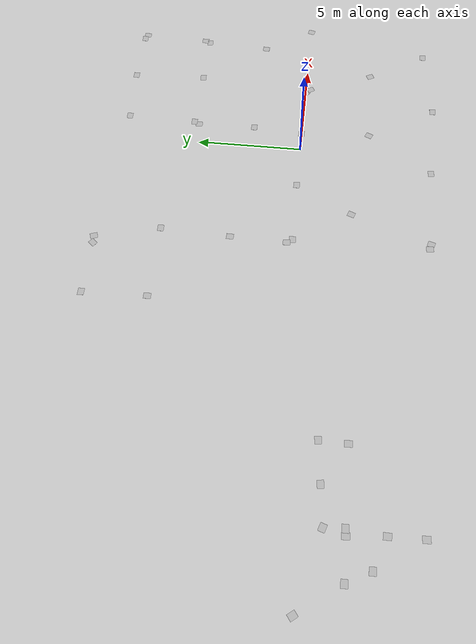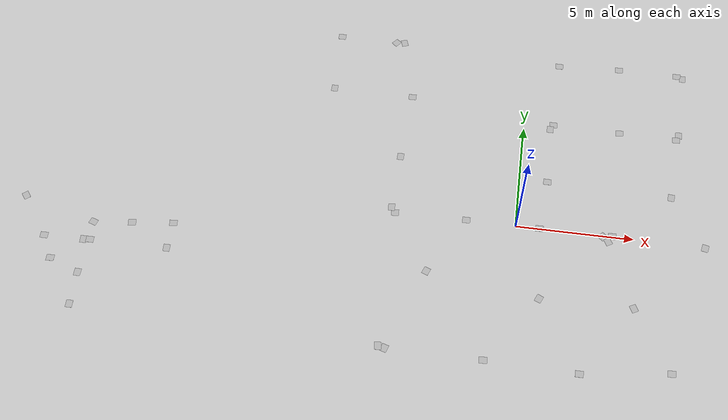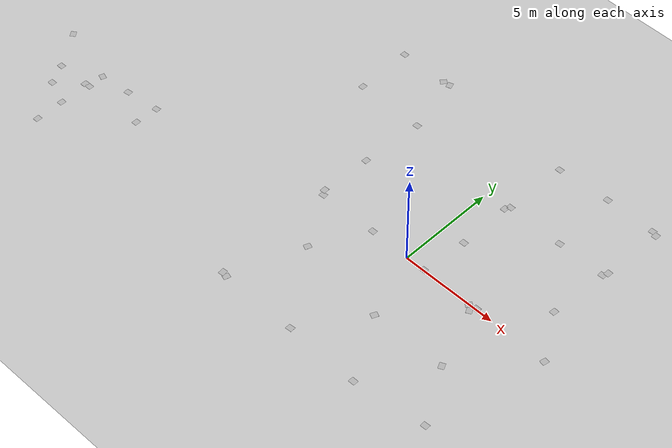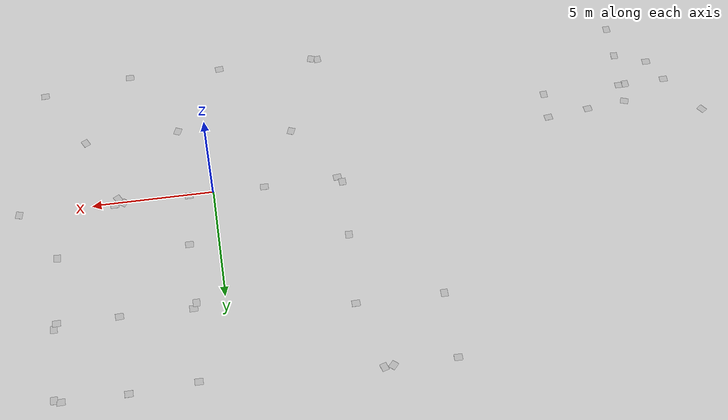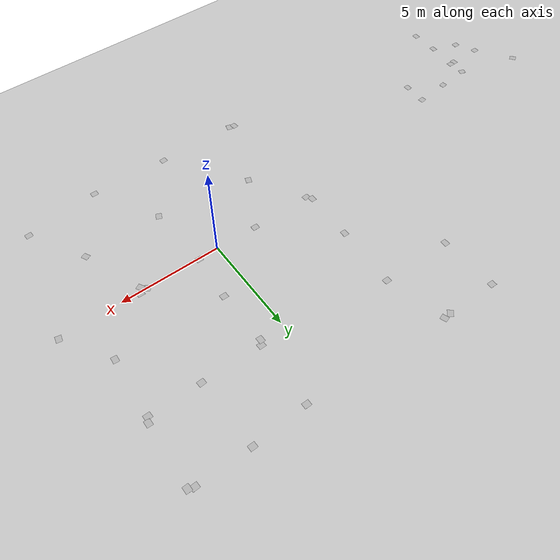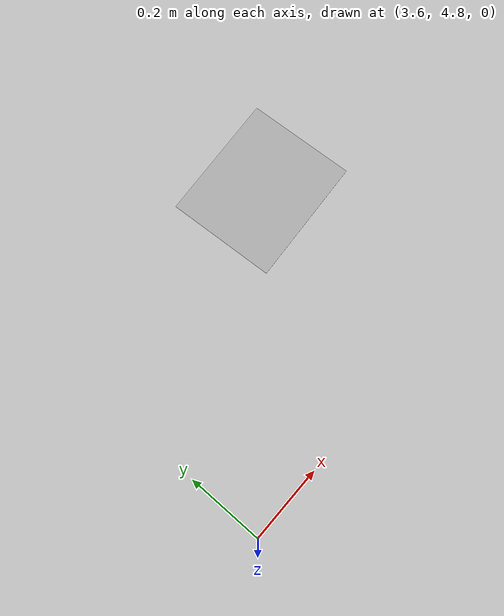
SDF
<sdf version="1.7">
 <world name="default">
  <light name="sun" type="directional">
   <pose>0 0 10 0 -0 0</pose>
   <diffuse>0.8 0.8 0.8 1</diffuse>
   <specular>0.1 0.1 0.1 1</specular>
   <attenuation>
    <range>1000</range>
    <constant>0.9</constant>
    <linear>0.01</linear>
    <quadratic>0.001</quadratic>
   </attenuation>
   <direction>-0.5 0.5 -1</direction>
   <spot><inner_angle>0</inner_angle><outer_angle>0</outer_angle><falloff>0</falloff></spot>
  </light>
  <model name="ground_plane">
   <static>1</static>
   <link name="link">
    <collision name="collision">
     <geometry><plane><normal>0 0 1</normal><size>100 100</size></plane></geometry>
     <surface><friction><ode><mu>100</mu><mu2>50</mu2></ode></friction></surface>
    </collision>
    <visual name="visual">
     <cast_shadows>0</cast_shadows>
     <geometry><plane><normal>0 0 1</normal><size>100 100</size></plane></geometry>
     <material>
      <script><uri>file://media/materials/scripts/gazebo.material</uri><name>Gazebo/Grey</name></script>
     </material>
    </visual>
   </link>
  </model>
  <gravity>0 0 -9.8</gravity>
  <magnetic_field>6e-06 2.3e-05 -4.2e-05</magnetic_field>
  <atmosphere type="adiabatic"/>
  <physics name="default_physics" default="0" type="ode">
   <max_step_size>0.001</max_step_size>
   <real_time_factor>1</real_time_factor>
   <real_time_update_rate>1000</real_time_update_rate>
  </physics>
  <scene><ambient>0.4 0.4 0.4 1</ambient><background>0.7 0.7 0.7 1</background><shadows>1</shadows></scene>
  <spherical_coordinates>
   <surface_model>EARTH_WGS84</surface_model>
   <latitude_deg>0</latitude_deg>
   <longitude_deg>0</longitude_deg>
   <elevation>0</elevation>
   <heading_deg>0</heading_deg>
  </spherical_coordinates>
  <audio><device>default</device></audio>
  <model name="stag-2000">
   <link name="link">
    <inertial>
     <mass>1</mass>
     <inertia><ixx>0.19</ixx><ixy>0</ixy><ixz>0</ixz><iyy>0.19</iyy><iyz>0</iyz><izz>0.19</izz></inertia>
    </inertial>
    <visual name="visual">
     <geometry><box><size>0.335 0.285 0.001</size></box></geometry>
     <material>
      <script>
       <uri>model://GO-stag-2000/material/scripts</uri>
       <uri>model://GO-stag-2000/material/texture</uri>
       <name>stag-2000/Diffuse</name>
      </script>
     </material>
    </visual>
    <collision name="collision">
     <geometry><box><size>0.335 0.285 0.001</size></box></geometry>
     <surface>
      <friction>
       <ode><mu>1</mu><mu2>1</mu2><fdir1>0 0 0</fdir1><slip1>0</slip1><slip2>0</slip2></ode>
       <torsional>
        <coefficient>1</coefficient>
        <patch_radius>0</patch_radius>
        <surface_radius>0</surface_radius>
        <use_patch_radius>1</use_patch_radius>
        <ode><slip>0</slip></ode>
       </torsional>
      </friction>
      <bounce><restitution_coefficient>0</restitution_coefficient><threshold>1e+06</threshold></bounce>
      <contact>
       <collide_without_contact>0</collide_without_contact>
       <collide_without_contact_bitmask>1</collide_without_contact_bitmask>
       <collide_bitmask>1</collide_bitmask>
       <ode>
        <soft_cfm>0</soft_cfm>
        <soft_erp>0.2</soft_erp>
        <kp>1e+13</kp>
        <kd>1</kd>
        <max_vel>0.01</max_vel>
        <min_depth>0</min_depth>
       </ode>
       <bullet>
        <split_impulse>1</split_impulse>
        <split_impulse_penetration_threshold>-0.01</split_impulse_penetration_threshold>
        <soft_cfm>0</soft_cfm>
        <soft_erp>0.2</soft_erp>
        <kp>1e+13</kp>
        <kd>1</kd>
       </bullet>
      </contact>
     </surface>
    </collision>
   </link>
   <static>1</static>
   <pose>1.00946 0.035142 0 0 -0 0</pose>
  </model>
  <model name="stag-500">
   <link name="link">
    <inertial>
     <mass>1</mass>
     <inertia><ixx>0.19</ixx><ixy>0</ixy><ixz>0</ixz><iyy>0.19</iyy><iyz>0</iyz><izz>0.19</izz></inertia>
    </inertial>
    <visual name="visual">
     <geometry><box><size>0.335 0.285 0.001</size></box></geometry>
     <material>
      <script>
       <uri>model://TURN-stag-500/material/scripts</uri>
       <uri>model://TURN-stag-500/material/texture</uri>
       <name>stag-500/Diffuse</name>
      </script>
     </material>
    </visual>
    <collision name="collision">
     <geometry><box><size>0.335 0.285 0.001</size></box></geometry>
     <surface>
      <friction>
       <ode><mu>1</mu><mu2>1</mu2><fdir1>0 0 0</fdir1><slip1>0</slip1><slip2>0</slip2></ode>
       <torsional>
        <coefficient>1</coefficient>
        <patch_radius>0</patch_radius>
        <surface_radius>0</surface_radius>
        <use_patch_radius>1</use_patch_radius>
        <ode><slip>0</slip></ode>
       </torsional>
      </friction>
      <bounce><restitution_coefficient>0</restitution_coefficient><threshold>1e+06</threshold></bounce>
      <contact>
       <collide_without_contact>0</collide_without_contact>
       <collide_without_contact_bitmask>1</collide_without_contact_bitmask>
       <collide_bitmask>1</collide_bitmask>
       <ode>
        <soft_cfm>0</soft_cfm>
        <soft_erp>0.2</soft_erp>
        <kp>1e+13</kp>
        <kd>1</kd>
        <max_vel>0.01</max_vel>
        <min_depth>0</min_depth>
       </ode>
       <bullet>
        <split_impulse>1</split_impulse>
        <split_impulse_penetration_threshold>-0.01</split_impulse_penetration_threshold>
        <soft_cfm>0</soft_cfm>
        <soft_erp>0.2</soft_erp>
        <kp>1e+13</kp>
        <kd>1</kd>
       </bullet>
      </contact>
     </surface>
    </collision>
   </link>
   <static>1</static>
   <pose>3.6975 -0.006963 0 0 0 -2.22259</pose>
  </model>
  <model name="stag-501">
   <link name="link">
    <inertial>
     <mass>1</mass>
     <inertia><ixx>0.19</ixx><ixy>0</ixy><ixz>0</ixz><iyy>0.19</iyy><iyz>0</iyz><izz>0.19</izz></inertia>
    </inertial>
    <visual name="visual">
     <geometry><box><size>0.335 0.285 0.001</size></box></geometry>
     <material>
      <script>
       <uri>model://TURN-stag-501/material/scripts</uri>
       <uri>model://TURN-stag-501/material/texture</uri>
       <name>stag-501/Diffuse</name>
      </script>
     </material>
    </visual>
    <collision name="collision">
     <geometry><box><size>0.335 0.285 0.001</size></box></geometry>
     <surface>
      <friction>
       <ode><mu>1</mu><mu2>1</mu2><fdir1>0 0 0</fdir1><slip1>0</slip1><slip2>0</slip2></ode>
       <torsional>
        <coefficient>1</coefficient>
        <patch_radius>0</patch_radius>
        <surface_radius>0</surface_radius>
        <use_patch_radius>1</use_patch_radius>
        <ode><slip>0</slip></ode>
       </torsional>
      </friction>
      <bounce><restitution_coefficient>0</restitution_coefficient><threshold>1e+06</threshold></bounce>
      <contact>
       <collide_without_contact>0</collide_without_contact>
       <collide_without_contact_bitmask>1</collide_without_contact_bitmask>
       <collide_bitmask>1</collide_bitmask>
       <ode>
        <soft_cfm>0</soft_cfm>
        <soft_erp>0.2</soft_erp>
        <kp>1e+13</kp>
        <kd>1</kd>
        <max_vel>0.01</max_vel>
        <min_depth>0</min_depth>
       </ode>
       <bullet>
        <split_impulse>1</split_impulse>
        <split_impulse_penetration_threshold>-0.01</split_impulse_penetration_threshold>
        <soft_cfm>0</soft_cfm>
        <soft_erp>0.2</soft_erp>
        <kp>1e+13</kp>
        <kd>1</kd>
       </bullet>
      </contact>
     </surface>
    </collision>
   </link>
   <static>1</static>
   <pose>3.9308 -0.226003 0 0 0 -1.0668</pose>
  </model>
  <model name="stag-2001">
   <link name="link">
    <inertial>
     <mass>1</mass>
     <inertia><ixx>0.19</ixx><ixy>0</ixy><ixz>0</ixz><iyy>0.19</iyy><iyz>0</iyz><izz>0.19</izz></inertia>
    </inertial>
    <visual name="visual">
     <geometry><box><size>0.335 0.285 0.001</size></box></geometry>
     <material>
      <script>
       <uri>model://GO-stag-2001/material/scripts</uri>
       <uri>model://GO-stag-2001/material/texture</uri>
       <name>stag-2001/Diffuse</name>
      </script>
     </material>
    </visual>
    <collision name="collision">
     <geometry><box><size>0.335 0.285 0.001</size></box></geometry>
     <surface>
      <friction>
       <ode><mu>1</mu><mu2>1</mu2><fdir1>0 0 0</fdir1><slip1>0</slip1><slip2>0</slip2></ode>
       <torsional>
        <coefficient>1</coefficient>
        <patch_radius>0</patch_radius>
        <surface_radius>0</surface_radius>
        <use_patch_radius>1</use_patch_radius>
        <ode><slip>0</slip></ode>
       </torsional>
      </friction>
      <bounce><restitution_coefficient>0</restitution_coefficient><threshold>1e+06</threshold></bounce>
      <contact>
       <collide_without_contact>0</collide_without_contact>
       <collide_without_contact_bitmask>1</collide_without_contact_bitmask>
       <collide_bitmask>1</collide_bitmask>
       <ode>
        <soft_cfm>0</soft_cfm>
        <soft_erp>0.2</soft_erp>
        <kp>1e+13</kp>
        <kd>1</kd>
        <max_vel>0.01</max_vel>
        <min_depth>0</min_depth>
       </ode>
       <bullet>
        <split_impulse>1</split_impulse>
        <split_impulse_penetration_threshold>-0.01</split_impulse_penetration_threshold>
        <soft_cfm>0</soft_cfm>
        <soft_erp>0.2</soft_erp>
        <kp>1e+13</kp>
        <kd>1</kd>
       </bullet>
      </contact>
     </surface>
    </collision>
   </link>
   <static>1</static>
   <pose>-0.859211 -6.31872 0 0 0 -3.05789</pose>
  </model>
  <model name="stag-502">
   <link name="link">
    <inertial>
     <mass>1</mass>
     <inertia><ixx>0.19</ixx><ixy>0</ixy><ixz>0</ixz><iyy>0.19</iyy><iyz>0</iyz><izz>0.19</izz></inertia>
    </inertial>
    <visual name="visual">
     <geometry><box><size>0.335 0.285 0.001</size></box></geometry>
     <material>
      <script>
       <uri>model://TURN-stag-502/material/scripts</uri>
       <uri>model://TURN-stag-502/material/texture</uri>
       <name>stag-502/Diffuse</name>
      </script>
     </material>
    </visual>
    <collision name="collision">
     <geometry><box><size>0.335 0.285 0.001</size></box></geometry>
     <surface>
      <friction>
       <ode><mu>1</mu><mu2>1</mu2><fdir1>0 0 0</fdir1><slip1>0</slip1><slip2>0</slip2></ode>
       <torsional>
        <coefficient>1</coefficient>
        <patch_radius>0</patch_radius>
        <surface_radius>0</surface_radius>
        <use_patch_radius>1</use_patch_radius>
        <ode><slip>0</slip></ode>
       </torsional>
      </friction>
      <bounce><restitution_coefficient>0</restitution_coefficient><threshold>1e+06</threshold></bounce>
      <contact>
       <collide_without_contact>0</collide_without_contact>
       <collide_without_contact_bitmask>1</collide_without_contact_bitmask>
       <collide_bitmask>1</collide_bitmask>
       <ode>
        <soft_cfm>0</soft_cfm>
        <soft_erp>0.2</soft_erp>
        <kp>1e+13</kp>
        <kd>1</kd>
        <max_vel>0.01</max_vel>
        <min_depth>0</min_depth>
       </ode>
       <bullet>
        <split_impulse>1</split_impulse>
        <split_impulse_penetration_threshold>-0.01</split_impulse_penetration_threshold>
        <soft_cfm>0</soft_cfm>
        <soft_erp>0.2</soft_erp>
        <kp>1e+13</kp>
        <kd>1</kd>
       </bullet>
      </contact>
     </surface>
    </collision>
   </link>
   <static>1</static>
   <pose>-4.87125 -6.31886 0 0 -0 1.27928</pose>
  </model>
  <model name="stag-503">
   <link name="link">
    <inertial>
     <mass>1</mass>
     <inertia><ixx>0.19</ixx><ixy>0</ixy><ixz>0</ixz><iyy>0.19</iyy><iyz>0</iyz><izz>0.19</izz></inertia>
    </inertial>
    <visual name="visual">
     <geometry><box><size>0.335 0.285 0.001</size></box></geometry>
     <material>
      <script>
       <uri>model://TURN-stag-503/material/scripts</uri>
       <uri>model://TURN-stag-503/material/texture</uri>
       <name>stag-503/Diffuse</name>
      </script>
     </material>
    </visual>
    <collision name="collision">
     <geometry><box><size>0.335 0.285 0.001</size></box></geometry>
     <surface>
      <friction>
       <ode><mu>1</mu><mu2>1</mu2><fdir1>0 0 0</fdir1><slip1>0</slip1><slip2>0</slip2></ode>
       <torsional>
        <coefficient>1</coefficient>
        <patch_radius>0</patch_radius>
        <surface_radius>0</surface_radius>
        <use_patch_radius>1</use_patch_radius>
        <ode><slip>0</slip></ode>
       </torsional>
      </friction>
      <bounce><restitution_coefficient>0</restitution_coefficient><threshold>1e+06</threshold></bounce>
      <contact>
       <collide_without_contact>0</collide_without_contact>
       <collide_without_contact_bitmask>1</collide_without_contact_bitmask>
       <collide_bitmask>1</collide_bitmask>
       <ode>
        <soft_cfm>0</soft_cfm>
        <soft_erp>0.2</soft_erp>
        <kp>1e+13</kp>
        <kd>1</kd>
        <max_vel>0.01</max_vel>
        <min_depth>0</min_depth>
       </ode>
       <bullet>
        <split_impulse>1</split_impulse>
        <split_impulse_penetration_threshold>-0.01</split_impulse_penetration_threshold>
        <soft_cfm>0</soft_cfm>
        <soft_erp>0.2</soft_erp>
        <kp>1e+13</kp>
        <kd>1</kd>
       </bullet>
      </contact>
     </surface>
    </collision>
   </link>
   <static>1</static>
   <pose>6.6827 -5.92098 0 0 0 -3.09858</pose>
  </model>
  <model name="stag-504">
   <link name="link">
    <inertial>
     <mass>1</mass>
     <inertia><ixx>0.19</ixx><ixy>0</ixy><ixz>0</ixz><iyy>0.19</iyy><iyz>0</iyz><izz>0.19</izz></inertia>
    </inertial>
    <visual name="visual">
     <geometry><box><size>0.335 0.285 0.001</size></box></geometry>
     <material>
      <script>
       <uri>model://TURN-stag-504/material/scripts</uri>
       <uri>model://TURN-stag-504/material/texture</uri>
       <name>stag-504/Diffuse</name>
      </script>
     </material>
    </visual>
    <collision name="collision">
     <geometry><box><size>0.335 0.285 0.001</size></box></geometry>
     <surface>
      <friction>
       <ode><mu>1</mu><mu2>1</mu2><fdir1>0 0 0</fdir1><slip1>0</slip1><slip2>0</slip2></ode>
       <torsional>
        <coefficient>1</coefficient>
        <patch_radius>0</patch_radius>
        <surface_radius>0</surface_radius>
        <use_patch_radius>1</use_patch_radius>
        <ode><slip>0</slip></ode>
       </torsional>
      </friction>
      <bounce><restitution_coefficient>0</restitution_coefficient><threshold>1e+06</threshold></bounce>
      <contact>
       <collide_without_contact>0</collide_without_contact>
       <collide_without_contact_bitmask>1</collide_without_contact_bitmask>
       <collide_bitmask>1</collide_bitmask>
       <ode>
        <soft_cfm>0</soft_cfm>
        <soft_erp>0.2</soft_erp>
        <kp>1e+13</kp>
        <kd>1</kd>
        <max_vel>0.01</max_vel>
        <min_depth>0</min_depth>
       </ode>
       <bullet>
        <split_impulse>1</split_impulse>
        <split_impulse_penetration_threshold>-0.01</split_impulse_penetration_threshold>
        <soft_cfm>0</soft_cfm>
        <soft_erp>0.2</soft_erp>
        <kp>1e+13</kp>
        <kd>1</kd>
       </bullet>
      </contact>
     </surface>
    </collision>
   </link>
   <static>1</static>
   <pose>-5.14523 -6.25426 0 0 -0 1.67214</pose>
  </model>
  <model name="stag-505">
   <link name="link">
    <inertial>
     <mass>1</mass>
     <inertia><ixx>0.19</ixx><ixy>0</ixy><ixz>0</ixz><iyy>0.19</iyy><iyz>0</iyz><izz>0.19</izz></inertia>
    </inertial>
    <visual name="visual">
     <geometry><box><size>0.335 0.285 0.001</size></box></geometry>
     <material>
      <script>
       <uri>model://TURN-stag-505/material/scripts</uri>
       <uri>model://TURN-stag-505/material/texture</uri>
       <name>stag-505/Diffuse</name>
      </script>
     </material>
    </visual>
    <collision name="collision">
     <geometry><box><size>0.335 0.285 0.001</size></box></geometry>
     <surface>
      <friction>
       <ode><mu>1</mu><mu2>1</mu2><fdir1>0 0 0</fdir1><slip1>0</slip1><slip2>0</slip2></ode>
       <torsional>
        <coefficient>1</coefficient>
        <patch_radius>0</patch_radius>
        <surface_radius>0</surface_radius>
        <use_patch_radius>1</use_patch_radius>
        <ode><slip>0</slip></ode>
       </torsional>
      </friction>
      <bounce><restitution_coefficient>0</restitution_coefficient><threshold>1e+06</threshold></bounce>
      <contact>
       <collide_without_contact>0</collide_without_contact>
       <collide_without_contact_bitmask>1</collide_without_contact_bitmask>
       <collide_bitmask>1</collide_bitmask>
       <ode>
        <soft_cfm>0</soft_cfm>
        <soft_erp>0.2</soft_erp>
        <kp>1e+13</kp>
        <kd>1</kd>
        <max_vel>0.01</max_vel>
        <min_depth>0</min_depth>
       </ode>
       <bullet>
        <split_impulse>1</split_impulse>
        <split_impulse_penetration_threshold>-0.01</split_impulse_penetration_threshold>
        <soft_cfm>0</soft_cfm>
        <soft_erp>0.2</soft_erp>
        <kp>1e+13</kp>
        <kd>1</kd>
       </bullet>
      </contact>
     </surface>
    </collision>
   </link>
   <static>1</static>
   <pose>-5.19033 -0.009099 0 -0.000184 -0.002064 0.08882</pose>
  </model>
  <model name="stag-2003">
   <link name="link">
    <inertial>
     <mass>1</mass>
     <inertia><ixx>0.19</ixx><ixy>0</ixy><ixz>0</ixz><iyy>0.19</iyy><iyz>0</iyz><izz>0.19</izz></inertia>
    </inertial>
    <visual name="visual">
     <geometry><box><size>0.335 0.285 0.001</size></box></geometry>
     <material>
      <script>
       <uri>model://GO-stag-2003/material/scripts</uri>
       <uri>model://GO-stag-2003/material/texture</uri>
       <name>stag-2003/Diffuse</name>
      </script>
     </material>
    </visual>
    <collision name="collision">
     <geometry><box><size>0.335 0.285 0.001</size></box></geometry>
     <surface>
      <friction>
       <ode><mu>1</mu><mu2>1</mu2><fdir1>0 0 0</fdir1><slip1>0</slip1><slip2>0</slip2></ode>
       <torsional>
        <coefficient>1</coefficient>
        <patch_radius>0</patch_radius>
        <surface_radius>0</surface_radius>
        <use_patch_radius>1</use_patch_radius>
        <ode><slip>0</slip></ode>
       </torsional>
      </friction>
      <bounce><restitution_coefficient>0</restitution_coefficient><threshold>1e+06</threshold></bounce>
      <contact>
       <collide_without_contact>0</collide_without_contact>
       <collide_without_contact_bitmask>1</collide_without_contact_bitmask>
       <collide_bitmask>1</collide_bitmask>
       <ode>
        <soft_cfm>0</soft_cfm>
        <soft_erp>0.2</soft_erp>
        <kp>1e+13</kp>
        <kd>1</kd>
        <max_vel>0.01</max_vel>
        <min_depth>0</min_depth>
       </ode>
       <bullet>
        <split_impulse>1</split_impulse>
        <split_impulse_penetration_threshold>-0.01</split_impulse_penetration_threshold>
        <soft_cfm>0</soft_cfm>
        <soft_erp>0.2</soft_erp>
        <kp>1e+13</kp>
        <kd>1</kd>
       </bullet>
      </contact>
     </surface>
    </collision>
   </link>
   <static>1</static>
   <pose>-2.12113 0.034986 0 0 -0 0</pose>
  </model>
  <model name="stag-2002">
   <link name="link">
    <inertial>
     <mass>1</mass>
     <inertia><ixx>0.19</ixx><ixy>0</ixy><ixz>0</ixz><iyy>0.19</iyy><iyz>0</iyz><izz>0.19</izz></inertia>
    </inertial>
    <visual name="visual">
     <geometry><box><size>0.335 0.285 0.001</size></box></geometry>
     <material>
      <script>
       <uri>model://GO-stag-2002/material/scripts</uri>
       <uri>model://GO-stag-2002/material/texture</uri>
       <name>stag-2002/Diffuse</name>
      </script>
     </material>
    </visual>
    <collision name="collision">
     <geometry><box><size>0.335 0.285 0.001</size></box></geometry>
     <surface>
      <friction>
       <ode><mu>1</mu><mu2>1</mu2><fdir1>0 0 0</fdir1><slip1>0</slip1><slip2>0</slip2></ode>
       <torsional>
        <coefficient>1</coefficient>
        <patch_radius>0</patch_radius>
        <surface_radius>0</surface_radius>
        <use_patch_radius>1</use_patch_radius>
        <ode><slip>0</slip></ode>
       </torsional>
      </friction>
      <bounce><restitution_coefficient>0</restitution_coefficient><threshold>1e+06</threshold></bounce>
      <contact>
       <collide_without_contact>0</collide_without_contact>
       <collide_without_contact_bitmask>1</collide_without_contact_bitmask>
       <collide_bitmask>1</collide_bitmask>
       <ode>
        <soft_cfm>0</soft_cfm>
        <soft_erp>0.2</soft_erp>
        <kp>1e+13</kp>
        <kd>1</kd>
        <max_vel>0.01</max_vel>
        <min_depth>0</min_depth>
       </ode>
       <bullet>
        <split_impulse>1</split_impulse>
        <split_impulse_penetration_threshold>-0.01</split_impulse_penetration_threshold>
        <soft_cfm>0</soft_cfm>
        <soft_erp>0.2</soft_erp>
        <kp>1e+13</kp>
        <kd>1</kd>
       </bullet>
      </contact>
     </surface>
    </collision>
   </link>
   <static>1</static>
   <pose>1.19885 -3.28434 0 0 0 -1.9888</pose>
  </model>
  <model name="stag-2004">
   <link name="link">
    <inertial>
     <mass>1</mass>
     <inertia><ixx>0.19</ixx><ixy>0</ixy><ixz>0</ixz><iyy>0.19</iyy><iyz>0</iyz><izz>0.19</izz></inertia>
    </inertial>
    <visual name="visual">
     <geometry><box><size>0.335 0.285 0.001</size></box></geometry>
     <material>
      <script>
       <uri>model://GO-stag-2004/material/scripts</uri>
       <uri>model://GO-stag-2004/material/texture</uri>
       <name>stag-2004/Diffuse</name>
      </script>
     </material>
    </visual>
    <collision name="collision">
     <geometry><box><size>0.335 0.285 0.001</size></box></geometry>
     <surface>
      <friction>
       <ode><mu>1</mu><mu2>1</mu2><fdir1>0 0 0</fdir1><slip1>0</slip1><slip2>0</slip2></ode>
       <torsional>
        <coefficient>1</coefficient>
        <patch_radius>0</patch_radius>
        <surface_radius>0</surface_radius>
        <use_patch_radius>1</use_patch_radius>
        <ode><slip>0</slip></ode>
       </torsional>
      </friction>
      <bounce><restitution_coefficient>0</restitution_coefficient><threshold>1e+06</threshold></bounce>
      <contact>
       <collide_without_contact>0</collide_without_contact>
       <collide_without_contact_bitmask>1</collide_without_contact_bitmask>
       <collide_bitmask>1</collide_bitmask>
       <ode>
        <soft_cfm>0</soft_cfm>
        <soft_erp>0.2</soft_erp>
        <kp>1e+13</kp>
        <kd>1</kd>
        <max_vel>0.01</max_vel>
        <min_depth>0</min_depth>
       </ode>
       <bullet>
        <split_impulse>1</split_impulse>
        <split_impulse_penetration_threshold>-0.01</split_impulse_penetration_threshold>
        <soft_cfm>0</soft_cfm>
        <soft_erp>0.2</soft_erp>
        <kp>1e+13</kp>
        <kd>1</kd>
       </bullet>
      </contact>
     </surface>
    </collision>
   </link>
   <static>1</static>
   <pose>5.09901 -3.22279 0 0 0 -1.11077</pose>
  </model>
  <model name="stag-2005">
   <link name="link">
    <inertial>
     <mass>1</mass>
     <inertia><ixx>0.19</ixx><ixy>0</ixy><ixz>0</ixz><iyy>0.19</iyy><iyz>0</iyz><izz>0.19</izz></inertia>
    </inertial>
    <visual name="visual">
     <geometry><box><size>0.335 0.285 0.001</size></box></geometry>
     <material>
      <script>
       <uri>model://GO-stag-2005/material/scripts</uri>
       <uri>model://GO-stag-2005/material/texture</uri>
       <name>stag-2005/Diffuse</name>
      </script>
     </material>
    </visual>
    <collision name="collision">
     <geometry><box><size>0.335 0.285 0.001</size></box></geometry>
     <surface>
      <friction>
       <ode><mu>1</mu><mu2>1</mu2><fdir1>0 0 0</fdir1><slip1>0</slip1><slip2>0</slip2></ode>
       <torsional>
        <coefficient>1</coefficient>
        <patch_radius>0</patch_radius>
        <surface_radius>0</surface_radius>
        <use_patch_radius>1</use_patch_radius>
        <ode><slip>0</slip></ode>
       </torsional>
      </friction>
      <bounce><restitution_coefficient>0</restitution_coefficient><threshold>1e+06</threshold></bounce>
      <contact>
       <collide_without_contact>0</collide_without_contact>
       <collide_without_contact_bitmask>1</collide_without_contact_bitmask>
       <collide_bitmask>1</collide_bitmask>
       <ode>
        <soft_cfm>0</soft_cfm>
        <soft_erp>0.2</soft_erp>
        <kp>1e+13</kp>
        <kd>1</kd>
        <max_vel>0.01</max_vel>
        <min_depth>0</min_depth>
       </ode>
       <bullet>
        <split_impulse>1</split_impulse>
        <split_impulse_penetration_threshold>-0.01</split_impulse_penetration_threshold>
        <soft_cfm>0</soft_cfm>
        <soft_erp>0.2</soft_erp>
        <kp>1e+13</kp>
        <kd>1</kd>
       </bullet>
      </contact>
     </surface>
    </collision>
   </link>
   <static>1</static>
   <pose>3.00845 -6.4097 0 0 -0 3.13807</pose>
  </model>
  <model name="stag-506">
   <link name="link">
    <inertial>
     <mass>1</mass>
     <inertia><ixx>0.19</ixx><ixy>0</ixy><ixz>0</ixz><iyy>0.19</iyy><iyz>0</iyz><izz>0.19</izz></inertia>
    </inertial>
    <visual name="visual">
     <geometry><box><size>0.335 0.285 0.001</size></box></geometry>
     <material>
      <script>
       <uri>model://TURN-stag-506/material/scripts</uri>
       <uri>model://TURN-stag-506/material/texture</uri>
       <name>stag-506/Diffuse</name>
      </script>
     </material>
    </visual>
    <collision name="collision">
     <geometry><box><size>0.335 0.285 0.001</size></box></geometry>
     <surface>
      <friction>
       <ode><mu>1</mu><mu2>1</mu2><fdir1>0 0 0</fdir1><slip1>0</slip1><slip2>0</slip2></ode>
       <torsional>
        <coefficient>1</coefficient>
        <patch_radius>0</patch_radius>
        <surface_radius>0</surface_radius>
        <use_patch_radius>1</use_patch_radius>
        <ode><slip>0</slip></ode>
       </torsional>
      </friction>
      <bounce><restitution_coefficient>0</restitution_coefficient><threshold>1e+06</threshold></bounce>
      <contact>
       <collide_without_contact>0</collide_without_contact>
       <collide_without_contact_bitmask>1</collide_without_contact_bitmask>
       <collide_bitmask>1</collide_bitmask>
       <ode>
        <soft_cfm>0</soft_cfm>
        <soft_erp>0.2</soft_erp>
        <kp>1e+13</kp>
        <kd>1</kd>
        <max_vel>0.01</max_vel>
        <min_depth>0</min_depth>
       </ode>
       <bullet>
        <split_impulse>1</split_impulse>
        <split_impulse_penetration_threshold>-0.01</split_impulse_penetration_threshold>
        <soft_cfm>0</soft_cfm>
        <soft_erp>0.2</soft_erp>
        <kp>1e+13</kp>
        <kd>1</kd>
       </bullet>
      </contact>
     </surface>
    </collision>
   </link>
   <static>1</static>
   <pose>4.08964 0.063668 0 0 -0 0</pose>
  </model>
  <model name="stag-507">
   <link name="link">
    <inertial>
     <mass>1</mass>
     <inertia><ixx>0.19</ixx><ixy>0</ixy><ixz>0</ixz><iyy>0.19</iyy><iyz>0</iyz><izz>0.19</izz></inertia>
    </inertial>
    <visual name="visual">
     <geometry><box><size>0.335 0.285 0.001</size></box></geometry>
     <material>
      <script>
       <uri>model://TURN-stag-507/material/scripts</uri>
       <uri>model://TURN-stag-507/material/texture</uri>
       <name>stag-507/Diffuse</name>
      </script>
     </material>
    </visual>
    <collision name="collision">
     <geometry><box><size>0.335 0.285 0.001</size></box></geometry>
     <surface>
      <friction>
       <ode><mu>1</mu><mu2>1</mu2><fdir1>0 0 0</fdir1><slip1>0</slip1><slip2>0</slip2></ode>
       <torsional>
        <coefficient>1</coefficient>
        <patch_radius>0</patch_radius>
        <surface_radius>0</surface_radius>
        <use_patch_radius>1</use_patch_radius>
        <ode><slip>0</slip></ode>
       </torsional>
      </friction>
      <bounce><restitution_coefficient>0</restitution_coefficient><threshold>1e+06</threshold></bounce>
      <contact>
       <collide_without_contact>0</collide_without_contact>
       <collide_without_contact_bitmask>1</collide_without_contact_bitmask>
       <collide_bitmask>1</collide_bitmask>
       <ode>
        <soft_cfm>0</soft_cfm>
        <soft_erp>0.2</soft_erp>
        <kp>1e+13</kp>
        <kd>1</kd>
        <max_vel>0.01</max_vel>
        <min_depth>0</min_depth>
       </ode>
       <bullet>
        <split_impulse>1</split_impulse>
        <split_impulse_penetration_threshold>-0.01</split_impulse_penetration_threshold>
        <soft_cfm>0</soft_cfm>
        <soft_erp>0.2</soft_erp>
        <kp>1e+13</kp>
        <kd>1</kd>
       </bullet>
      </contact>
     </surface>
    </collision>
   </link>
   <static>1</static>
   <pose>8.01455 -0.0043 0 0 0 -1.78121</pose>
  </model>
  <model name="stag-2006">
   <link name="link">
    <inertial>
     <mass>1</mass>
     <inertia><ixx>0.19</ixx><ixy>0</ixy><ixz>0</ixz><iyy>0.19</iyy><iyz>0</iyz><izz>0.19</izz></inertia>
    </inertial>
    <visual name="visual">
     <geometry><box><size>0.335 0.285 0.001</size></box></geometry>
     <material>
      <script>
       <uri>model://GO-stag-2006/material/scripts</uri>
       <uri>model://GO-stag-2006/material/texture</uri>
       <name>stag-2006/Diffuse</name>
      </script>
     </material>
    </visual>
    <collision name="collision">
     <geometry><box><size>0.335 0.285 0.001</size></box></geometry>
     <surface>
      <friction>
       <ode><mu>1</mu><mu2>1</mu2><fdir1>0 0 0</fdir1><slip1>0</slip1><slip2>0</slip2></ode>
       <torsional>
        <coefficient>1</coefficient>
        <patch_radius>0</patch_radius>
        <surface_radius>0</surface_radius>
        <use_patch_radius>1</use_patch_radius>
        <ode><slip>0</slip></ode>
       </torsional>
      </friction>
      <bounce><restitution_coefficient>0</restitution_coefficient><threshold>1e+06</threshold></bounce>
      <contact>
       <collide_without_contact>0</collide_without_contact>
       <collide_without_contact_bitmask>1</collide_without_contact_bitmask>
       <collide_bitmask>1</collide_bitmask>
       <ode>
        <soft_cfm>0</soft_cfm>
        <soft_erp>0.2</soft_erp>
        <kp>1e+13</kp>
        <kd>1</kd>
        <max_vel>0.01</max_vel>
        <min_depth>0</min_depth>
       </ode>
       <bullet>
        <split_impulse>1</split_impulse>
        <split_impulse_penetration_threshold>-0.01</split_impulse_penetration_threshold>
        <soft_cfm>0</soft_cfm>
        <soft_erp>0.2</soft_erp>
        <kp>1e+13</kp>
        <kd>1</kd>
       </bullet>
      </contact>
     </surface>
    </collision>
   </link>
   <static>1</static>
   <pose>-3.56 -2.62137 0 0 -0 1.20236</pose>
  </model>
  <model name="stag-508">
   <link name="link">
    <inertial>
     <mass>1</mass>
     <inertia><ixx>0.19</ixx><ixy>0</ixy><ixz>0</ixz><iyy>0.19</iyy><iyz>0</iyz><izz>0.19</izz></inertia>
    </inertial>
    <visual name="visual">
     <geometry><box><size>0.335 0.285 0.001</size></box></geometry>
     <material>
      <script>
       <uri>model://TURN-stag-508/material/scripts</uri>
       <uri>model://TURN-stag-508/material/texture</uri>
       <name>stag-508/Diffuse</name>
      </script>
     </material>
    </visual>
    <collision name="collision">
     <geometry><box><size>0.335 0.285 0.001</size></box></geometry>
     <surface>
      <friction>
       <ode><mu>1</mu><mu2>1</mu2><fdir1>0 0 0</fdir1><slip1>0</slip1><slip2>0</slip2></ode>
       <torsional>
        <coefficient>1</coefficient>
        <patch_radius>0</patch_radius>
        <surface_radius>0</surface_radius>
        <use_patch_radius>1</use_patch_radius>
        <ode><slip>0</slip></ode>
       </torsional>
      </friction>
      <bounce><restitution_coefficient>0</restitution_coefficient><threshold>1e+06</threshold></bounce>
      <contact>
       <collide_without_contact>0</collide_without_contact>
       <collide_without_contact_bitmask>1</collide_without_contact_bitmask>
       <collide_bitmask>1</collide_bitmask>
       <ode>
        <soft_cfm>0</soft_cfm>
        <soft_erp>0.2</soft_erp>
        <kp>1e+13</kp>
        <kd>1</kd>
        <max_vel>0.01</max_vel>
        <min_depth>0</min_depth>
       </ode>
       <bullet>
        <split_impulse>1</split_impulse>
        <split_impulse_penetration_threshold>-0.01</split_impulse_penetration_threshold>
        <soft_cfm>0</soft_cfm>
        <soft_erp>0.2</soft_erp>
        <kp>1e+13</kp>
        <kd>1</kd>
       </bullet>
      </contact>
     </surface>
    </collision>
   </link>
   <static>1</static>
   <pose>-5.36882 0.246675 0 0 -0 1.61151</pose>
  </model>
  <model name="stag-8000">
   <link name="link">
    <inertial>
     <mass>1</mass>
     <inertia><ixx>0.19</ixx><ixy>0</ixy><ixz>0</ixz><iyy>0.19</iyy><iyz>0</iyz><izz>0.19</izz></inertia>
    </inertial>
    <visual name="visual">
     <geometry><box><size>0.335 0.285 0.001</size></box></geometry>
     <material>
      <script>
       <uri>model://STOP-stag-8000/material/scripts</uri>
       <uri>model://STOP-stag-8000/material/texture</uri>
       <name>stag-8000/Diffuse</name>
      </script>
     </material>
    </visual>
    <collision name="collision">
     <geometry><box><size>0.335 0.285 0.001</size></box></geometry>
     <surface>
      <friction>
       <ode><mu>1</mu><mu2>1</mu2><fdir1>0 0 0</fdir1><slip1>0</slip1><slip2>0</slip2></ode>
       <torsional>
        <coefficient>1</coefficient>
        <patch_radius>0</patch_radius>
        <surface_radius>0</surface_radius>
        <use_patch_radius>1</use_patch_radius>
        <ode><slip>0</slip></ode>
       </torsional>
      </friction>
      <bounce><restitution_coefficient>0</restitution_coefficient><threshold>1e+06</threshold></bounce>
      <contact>
       <collide_without_contact>0</collide_without_contact>
       <collide_without_contact_bitmask>1</collide_without_contact_bitmask>
       <collide_bitmask>1</collide_bitmask>
       <ode>
        <soft_cfm>0</soft_cfm>
        <soft_erp>0.2</soft_erp>
        <kp>1e+13</kp>
        <kd>1</kd>
        <max_vel>0.01</max_vel>
        <min_depth>0</min_depth>
       </ode>
       <bullet>
        <split_impulse>1</split_impulse>
        <split_impulse_penetration_threshold>-0.01</split_impulse_penetration_threshold>
        <soft_cfm>0</soft_cfm>
        <soft_erp>0.2</soft_erp>
        <kp>1e+13</kp>
        <kd>1</kd>
       </bullet>
      </contact>
     </surface>
    </collision>
   </link>
   <static>1</static>
   <pose>-5.28529 2.85022 0 0 0 -1.59608</pose>
  </model>
  <model name="stag-7000">
   <link name="link">
    <inertial>
     <mass>1</mass>
     <inertia><ixx>0.19</ixx><ixy>0</ixy><ixz>0</ixz><iyy>0.19</iyy><iyz>0</iyz><izz>0.19</izz></inertia>
    </inertial>
    <visual name="visual">
     <geometry><box><size>0.335 0.285 0.001</size></box></geometry>
     <material>
      <script>
       <uri>model://BIDIR-stag-7000/material/scripts</uri>
       <uri>model://BIDIR-stag-7000/material/texture</uri>
       <name>stag-7000/Diffuse</name>
      </script>
     </material>
    </visual>
    <collision name="collision">
     <geometry><box><size>0.335 0.285 0.001</size></box></geometry>
     <surface>
      <friction>
       <ode><mu>1</mu><mu2>1</mu2><fdir1>0 0 0</fdir1><slip1>0</slip1><slip2>0</slip2></ode>
       <torsional>
        <coefficient>1</coefficient>
        <patch_radius>0</patch_radius>
        <surface_radius>0</surface_radius>
        <use_patch_radius>1</use_patch_radius>
        <ode><slip>0</slip></ode>
       </torsional>
      </friction>
      <bounce><restitution_coefficient>0</restitution_coefficient><threshold>1e+06</threshold></bounce>
      <contact>
       <collide_without_contact>0</collide_without_contact>
       <collide_without_contact_bitmask>1</collide_without_contact_bitmask>
       <collide_bitmask>1</collide_bitmask>
       <ode>
        <soft_cfm>0</soft_cfm>
        <soft_erp>0.2</soft_erp>
        <kp>1e+13</kp>
        <kd>1</kd>
        <max_vel>0.01</max_vel>
        <min_depth>0</min_depth>
       </ode>
       <bullet>
        <split_impulse>1</split_impulse>
        <split_impulse_penetration_threshold>-0.01</split_impulse_penetration_threshold>
        <soft_cfm>0</soft_cfm>
        <soft_erp>0.2</soft_erp>
        <kp>1e+13</kp>
        <kd>1</kd>
       </bullet>
      </contact>
     </surface>
    </collision>
   </link>
   <static>1</static>
   <pose>4.11074 8.80539 0 0 -0 0.017471</pose>
  </model>
  <model name="stag-7001">
   <link name="link">
    <inertial>
     <mass>1</mass>
     <inertia><ixx>0.19</ixx><ixy>0</ixy><ixz>0</ixz><iyy>0.19</iyy><iyz>0</iyz><izz>0.19</izz></inertia>
    </inertial>
    <visual name="visual">
     <geometry><box><size>0.335 0.285 0.001</size></box></geometry>
     <material>
      <script>
       <uri>model://BIDIR-stag-7001/material/scripts</uri>
       <uri>model://BIDIR-stag-7001/material/texture</uri>
       <name>stag-7001/Diffuse</name>
      </script>
     </material>
    </visual>
    <collision name="collision">
     <geometry><box><size>0.335 0.285 0.001</size></box></geometry>
     <surface>
      <friction>
       <ode><mu>1</mu><mu2>1</mu2><fdir1>0 0 0</fdir1><slip1>0</slip1><slip2>0</slip2></ode>
       <torsional>
        <coefficient>1</coefficient>
        <patch_radius>0</patch_radius>
        <surface_radius>0</surface_radius>
        <use_patch_radius>1</use_patch_radius>
        <ode><slip>0</slip></ode>
       </torsional>
      </friction>
      <bounce><restitution_coefficient>0</restitution_coefficient><threshold>1e+06</threshold></bounce>
      <contact>
       <collide_without_contact>0</collide_without_contact>
       <collide_without_contact_bitmask>1</collide_without_contact_bitmask>
       <collide_bitmask>1</collide_bitmask>
       <ode>
        <soft_cfm>0</soft_cfm>
        <soft_erp>0.2</soft_erp>
        <kp>1e+13</kp>
        <kd>1</kd>
        <max_vel>0.01</max_vel>
        <min_depth>0</min_depth>
       </ode>
       <bullet>
        <split_impulse>1</split_impulse>
        <split_impulse_penetration_threshold>-0.01</split_impulse_penetration_threshold>
        <soft_cfm>0</soft_cfm>
        <soft_erp>0.2</soft_erp>
        <kp>1e+13</kp>
        <kd>1</kd>
       </bullet>
      </contact>
     </surface>
    </collision>
   </link>
   <static>1</static>
   <pose>4.24411 5.34387 0 0 0 -3.08038</pose>
  </model>
  <model name="stag-8002">
   <link name="link">
    <inertial>
     <mass>1</mass>
     <inertia><ixx>0.19</ixx><ixy>0</ixy><ixz>0</ixz><iyy>0.19</iyy><iyz>0</iyz><izz>0.19</izz></inertia>
    </inertial>
    <visual name="visual">
     <geometry><box><size>0.335 0.285 0.001</size></box></geometry>
     <material>
      <script>
       <uri>model://STOP-stag-8002/material/scripts</uri>
       <uri>model://STOP-stag-8002/material/texture</uri>
       <name>stag-8002/Diffuse</name>
      </script>
     </material>
    </visual>
    <collision name="collision">
     <geometry><box><size>0.335 0.285 0.001</size></box></geometry>
     <surface>
      <friction>
       <ode><mu>1</mu><mu2>1</mu2><fdir1>0 0 0</fdir1><slip1>0</slip1><slip2>0</slip2></ode>
       <torsional>
        <coefficient>1</coefficient>
        <patch_radius>0</patch_radius>
        <surface_radius>0</surface_radius>
        <use_patch_radius>1</use_patch_radius>
        <ode><slip>0</slip></ode>
       </torsional>
      </friction>
      <bounce><restitution_coefficient>0</restitution_coefficient><threshold>1e+06</threshold></bounce>
      <contact>
       <collide_without_contact>0</collide_without_contact>
       <collide_without_contact_bitmask>1</collide_without_contact_bitmask>
       <collide_bitmask>1</collide_bitmask>
       <ode>
        <soft_cfm>0</soft_cfm>
        <soft_erp>0.2</soft_erp>
        <kp>1e+13</kp>
        <kd>1</kd>
        <max_vel>0.01</max_vel>
        <min_depth>0</min_depth>
       </ode>
       <bullet>
        <split_impulse>1</split_impulse>
        <split_impulse_penetration_threshold>-0.01</split_impulse_penetration_threshold>
        <soft_cfm>0</soft_cfm>
        <soft_erp>0.2</soft_erp>
        <kp>1e+13</kp>
        <kd>1</kd>
       </bullet>
      </contact>
     </surface>
    </collision>
   </link>
   <static>1</static>
   <pose>1.38481 8.66301 0 0 -0 0</pose>
  </model>
  <model name="stag-9">
   <link name="link">
    <inertial>
     <mass>1</mass>
     <inertia><ixx>0.19</ixx><ixy>0</ixy><ixz>0</ixz><iyy>0.19</iyy><iyz>0</iyz><izz>0.19</izz></inertia>
    </inertial>
    <visual name="visual">
     <geometry><box><size>0.335 0.285 0.001</size></box></geometry>
     <material>
      <script>
       <uri>model://TURN-stag-9/material/scripts</uri>
       <uri>model://TURN-stag-9/material/texture</uri>
       <name>stag-9/Diffuse</name>
      </script>
     </material>
    </visual>
    <collision name="collision">
     <geometry><box><size>0.335 0.285 0.001</size></box></geometry>
     <surface>
      <friction>
       <ode><mu>1</mu><mu2>1</mu2><fdir1>0 0 0</fdir1><slip1>0</slip1><slip2>0</slip2></ode>
       <torsional>
        <coefficient>1</coefficient>
        <patch_radius>0</patch_radius>
        <surface_radius>0</surface_radius>
        <use_patch_radius>1</use_patch_radius>
        <ode><slip>0</slip></ode>
       </torsional>
      </friction>
      <bounce><restitution_coefficient>0</restitution_coefficient><threshold>1e+06</threshold></bounce>
      <contact>
       <collide_without_contact>0</collide_without_contact>
       <collide_without_contact_bitmask>1</collide_without_contact_bitmask>
       <collide_bitmask>1</collide_bitmask>
       <ode>
        <soft_cfm>0</soft_cfm>
        <soft_erp>0.2</soft_erp>
        <kp>1e+13</kp>
        <kd>1</kd>
        <max_vel>0.01</max_vel>
        <min_depth>0</min_depth>
       </ode>
       <bullet>
        <split_impulse>1</split_impulse>
        <split_impulse_penetration_threshold>-0.01</split_impulse_penetration_threshold>
        <soft_cfm>0</soft_cfm>
        <soft_erp>0.2</soft_erp>
        <kp>1e+13</kp>
        <kd>1</kd>
       </bullet>
      </contact>
     </surface>
    </collision>
   </link>
   <static>1</static>
   <pose>6.72514 8.7904 0 0 0 -3.10739</pose>
  </model>
  <model name="stag-7">
   <link name="link">
    <inertial>
     <mass>1</mass>
     <inertia><ixx>0.19</ixx><ixy>0</ixy><ixz>0</ixz><iyy>0.19</iyy><iyz>0</iyz><izz>0.19</izz></inertia>
    </inertial>
    <visual name="visual">
     <geometry><box><size>0.335 0.285 0.001</size></box></geometry>
     <material>
      <script>
       <uri>model://TURN-stag-7/material/scripts</uri>
       <uri>model://TURN-stag-7/material/texture</uri>
       <name>stag-7/Diffuse</name>
      </script>
     </material>
    </visual>
    <collision name="collision">
     <geometry><box><size>0.335 0.285 0.001</size></box></geometry>
     <surface>
      <friction>
       <ode><mu>1</mu><mu2>1</mu2><fdir1>0 0 0</fdir1><slip1>0</slip1><slip2>0</slip2></ode>
       <torsional>
        <coefficient>1</coefficient>
        <patch_radius>0</patch_radius>
        <surface_radius>0</surface_radius>
        <use_patch_radius>1</use_patch_radius>
        <ode><slip>0</slip></ode>
       </torsional>
      </friction>
      <bounce><restitution_coefficient>0</restitution_coefficient><threshold>1e+06</threshold></bounce>
      <contact>
       <collide_without_contact>0</collide_without_contact>
       <collide_without_contact_bitmask>1</collide_without_contact_bitmask>
       <collide_bitmask>1</collide_bitmask>
       <ode>
        <soft_cfm>0</soft_cfm>
        <soft_erp>0.2</soft_erp>
        <kp>1e+13</kp>
        <kd>1</kd>
        <max_vel>0.01</max_vel>
        <min_depth>0</min_depth>
       </ode>
       <bullet>
        <split_impulse>1</split_impulse>
        <split_impulse_penetration_threshold>-0.01</split_impulse_penetration_threshold>
        <soft_cfm>0</soft_cfm>
        <soft_erp>0.2</soft_erp>
        <kp>1e+13</kp>
        <kd>1</kd>
       </bullet>
      </contact>
     </surface>
    </collision>
   </link>
   <static>1</static>
   <pose>6.98577 8.68503 0 0 0 -1.55286</pose>
  </model>
  <model name="stag-4">
   <link name="link">
    <inertial>
     <mass>1</mass>
     <inertia><ixx>0.19</ixx><ixy>0</ixy><ixz>0</ixz><iyy>0.19</iyy><iyz>0</iyz><izz>0.19</izz></inertia>
    </inertial>
    <visual name="visual">
     <geometry><box><size>0.335 0.285 0.001</size></box></geometry>
     <material>
      <script>
       <uri>model://TURN-stag-4/material/scripts</uri>
       <uri>model://TURN-stag-4/material/texture</uri>
       <name>stag-4/Diffuse</name>
      </script>
     </material>
    </visual>
    <collision name="collision">
     <geometry><box><size>0.335 0.285 0.001</size></box></geometry>
     <surface>
      <friction>
       <ode><mu>1</mu><mu2>1</mu2><fdir1>0 0 0</fdir1><slip1>0</slip1><slip2>0</slip2></ode>
       <torsional>
        <coefficient>1</coefficient>
        <patch_radius>0</patch_radius>
        <surface_radius>0</surface_radius>
        <use_patch_radius>1</use_patch_radius>
        <ode><slip>0</slip></ode>
       </torsional>
      </friction>
      <bounce><restitution_coefficient>0</restitution_coefficient><threshold>1e+06</threshold></bounce>
      <contact>
       <collide_without_contact>0</collide_without_contact>
       <collide_without_contact_bitmask>1</collide_without_contact_bitmask>
       <collide_bitmask>1</collide_bitmask>
       <ode>
        <soft_cfm>0</soft_cfm>
        <soft_erp>0.2</soft_erp>
        <kp>1e+13</kp>
        <kd>1</kd>
        <max_vel>0.01</max_vel>
        <min_depth>0</min_depth>
       </ode>
       <bullet>
        <split_impulse>1</split_impulse>
        <split_impulse_penetration_threshold>-0.01</split_impulse_penetration_threshold>
        <soft_cfm>0</soft_cfm>
        <soft_erp>0.2</soft_erp>
        <kp>1e+13</kp>
        <kd>1</kd>
       </bullet>
      </contact>
     </surface>
    </collision>
   </link>
   <static>1</static>
   <pose>3.66844 4.91263 -0.149948 0 -0 1.58321</pose>
  </model>
  <model name="stag-14">
   <link name="link">
    <inertial>
     <mass>1</mass>
     <inertia><ixx>0.19</ixx><ixy>0</ixy><ixz>0</ixz><iyy>0.19</iyy><iyz>0</iyz><izz>0.19</izz></inertia>
    </inertial>
    <visual name="visual">
     <geometry><box><size>0.335 0.285 0.001</size></box></geometry>
     <material>
      <script>
       <uri>model://TURN-stag-14/material/scripts</uri>
       <uri>model://TURN-stag-14/material/texture</uri>
       <name>stag-14/Diffuse</name>
      </script>
     </material>
    </visual>
    <collision name="collision">
     <geometry><box><size>0.335 0.285 0.001</size></box></geometry>
     <surface>
      <friction>
       <ode><mu>1</mu><mu2>1</mu2><fdir1>0 0 0</fdir1><slip1>0</slip1><slip2>0</slip2></ode>
       <torsional>
        <coefficient>1</coefficient>
        <patch_radius>0</patch_radius>
        <surface_radius>0</surface_radius>
        <use_patch_radius>1</use_patch_radius>
        <ode><slip>0</slip></ode>
       </torsional>
      </friction>
      <bounce><restitution_coefficient>0</restitution_coefficient><threshold>1e+06</threshold></bounce>
      <contact>
       <collide_without_contact>0</collide_without_contact>
       <collide_without_contact_bitmask>1</collide_without_contact_bitmask>
       <collide_bitmask>1</collide_bitmask>
       <ode>
        <soft_cfm>0</soft_cfm>
        <soft_erp>0.2</soft_erp>
        <kp>1e+13</kp>
        <kd>1</kd>
        <max_vel>0.01</max_vel>
        <min_depth>0</min_depth>
       </ode>
       <bullet>
        <split_impulse>1</split_impulse>
        <split_impulse_penetration_threshold>-0.01</split_impulse_penetration_threshold>
        <soft_cfm>0</soft_cfm>
        <soft_erp>0.2</soft_erp>
        <kp>1e+13</kp>
        <kd>1</kd>
       </bullet>
      </contact>
     </surface>
    </collision>
   </link>
   <static>1</static>
   <pose>6.85208 5.56319 0 0 -0 1.55348</pose>
  </model>
  <model name="stag-510">
   <link name="link">
    <inertial>
     <mass>1</mass>
     <inertia><ixx>0.19</ixx><ixy>0</ixy><ixz>0</ixz><iyy>0.19</iyy><iyz>0</iyz><izz>0.19</izz></inertia>
    </inertial>
    <visual name="visual">
     <geometry><box><size>0.335 0.285 0.001</size></box></geometry>
     <material>
      <script>
       <uri>model://TURN-stag-510/material/scripts</uri>
       <uri>model://TURN-stag-510/material/texture</uri>
       <name>stag-510/Diffuse</name>
      </script>
     </material>
    </visual>
    <collision name="collision">
     <geometry><box><size>0.335 0.285 0.001</size></box></geometry>
     <surface>
      <friction>
       <ode><mu>1</mu><mu2>1</mu2><fdir1>0 0 0</fdir1><slip1>0</slip1><slip2>0</slip2></ode>
       <torsional>
        <coefficient>1</coefficient>
        <patch_radius>0</patch_radius>
        <surface_radius>0</surface_radius>
        <use_patch_radius>1</use_patch_radius>
        <ode><slip>0</slip></ode>
       </torsional>
      </friction>
      <bounce><restitution_coefficient>0</restitution_coefficient><threshold>1e+06</threshold></bounce>
      <contact>
       <collide_without_contact>0</collide_without_contact>
       <collide_without_contact_bitmask>1</collide_without_contact_bitmask>
       <collide_bitmask>1</collide_bitmask>
       <ode>
        <soft_cfm>0</soft_cfm>
        <soft_erp>0.2</soft_erp>
        <kp>1e+13</kp>
        <kd>1</kd>
        <max_vel>0.01</max_vel>
        <min_depth>0</min_depth>
       </ode>
       <bullet>
        <split_impulse>1</split_impulse>
        <split_impulse_penetration_threshold>-0.01</split_impulse_penetration_threshold>
        <soft_cfm>0</soft_cfm>
        <soft_erp>0.2</soft_erp>
        <kp>1e+13</kp>
        <kd>1</kd>
       </bullet>
      </contact>
     </surface>
    </collision>
   </link>
   <static>1</static>
   <pose>6.73316 5.3055 0 0 0 -3.11023</pose>
  </model>
  <model name="stag-1">
   <link name="link">
    <inertial>
     <mass>1</mass>
     <inertia><ixx>0.19</ixx><ixy>0</ixy><ixz>0</ixz><iyy>0.19</iyy><iyz>0</iyz><izz>0.19</izz></inertia>
    </inertial>
    <visual name="visual">
     <geometry><box><size>0.335 0.285 0.001</size></box></geometry>
     <material>
      <script>
       <uri>model://TURN-stag-1/material/scripts</uri>
       <uri>model://TURN-stag-1/material/texture</uri>
       <name>stag-1/Diffuse</name>
      </script>
     </material>
    </visual>
    <collision name="collision">
     <geometry><box><size>0.335 0.285 0.001</size></box></geometry>
     <surface>
      <friction>
       <ode><mu>1</mu><mu2>1</mu2><fdir1>0 0 0</fdir1><slip1>0</slip1><slip2>0</slip2></ode>
       <torsional>
        <coefficient>1</coefficient>
        <patch_radius>0</patch_radius>
        <surface_radius>0</surface_radius>
        <use_patch_radius>1</use_patch_radius>
        <ode><slip>0</slip></ode>
       </torsional>
      </friction>
      <bounce><restitution_coefficient>0</restitution_coefficient><threshold>1e+06</threshold></bounce>
      <contact>
       <collide_without_contact>0</collide_without_contact>
       <collide_without_contact_bitmask>1</collide_without_contact_bitmask>
       <collide_bitmask>1</collide_bitmask>
       <ode>
        <soft_cfm>0</soft_cfm>
        <soft_erp>0.2</soft_erp>
        <kp>1e+13</kp>
        <kd>1</kd>
        <max_vel>0.01</max_vel>
        <min_depth>0</min_depth>
       </ode>
       <bullet>
        <split_impulse>1</split_impulse>
        <split_impulse_penetration_threshold>-0.01</split_impulse_penetration_threshold>
        <soft_cfm>0</soft_cfm>
        <soft_erp>0.2</soft_erp>
        <kp>1e+13</kp>
        <kd>1</kd>
       </bullet>
      </contact>
     </surface>
    </collision>
   </link>
   <static>1</static>
   <pose>1.29753 5.39359 0 0 -0 0</pose>
  </model>
  <model name="stag-16">
   <link name="link">
    <inertial>
     <mass>1</mass>
     <inertia><ixx>0.19</ixx><ixy>0</ixy><ixz>0</ixz><iyy>0.19</iyy><iyz>0</iyz><izz>0.19</izz></inertia>
    </inertial>
    <visual name="visual">
     <geometry><box><size>0.335 0.285 0.001</size></box></geometry>
     <material>
      <script>
       <uri>model://TURN-stag-16/material/scripts</uri>
       <uri>model://TURN-stag-16/material/texture</uri>
       <name>stag-16/Diffuse</name>
      </script>
     </material>
    </visual>
    <collision name="collision">
     <geometry><box><size>0.335 0.285 0.001</size></box></geometry>
     <surface>
      <friction>
       <ode><mu>1</mu><mu2>1</mu2><fdir1>0 0 0</fdir1><slip1>0</slip1><slip2>0</slip2></ode>
       <torsional>
        <coefficient>1</coefficient>
        <patch_radius>0</patch_radius>
        <surface_radius>0</surface_radius>
        <use_patch_radius>1</use_patch_radius>
        <ode><slip>0</slip></ode>
       </torsional>
      </friction>
      <bounce><restitution_coefficient>0</restitution_coefficient><threshold>1e+06</threshold></bounce>
      <contact>
       <collide_without_contact>0</collide_without_contact>
       <collide_without_contact_bitmask>1</collide_without_contact_bitmask>
       <collide_bitmask>1</collide_bitmask>
       <ode>
        <soft_cfm>0</soft_cfm>
        <soft_erp>0.2</soft_erp>
        <kp>1e+13</kp>
        <kd>1</kd>
        <max_vel>0.01</max_vel>
        <min_depth>0</min_depth>
       </ode>
       <bullet>
        <split_impulse>1</split_impulse>
        <split_impulse_penetration_threshold>-0.01</split_impulse_penetration_threshold>
        <soft_cfm>0</soft_cfm>
        <soft_erp>0.2</soft_erp>
        <kp>1e+13</kp>
        <kd>1</kd>
       </bullet>
      </contact>
     </surface>
    </collision>
   </link>
   <static>1</static>
   <pose>1.16522 5.14746 0 0 0 -1.57872</pose>
  </model>
  <model name="stag-13">
   <link name="link">
    <inertial>
     <mass>1</mass>
     <inertia><ixx>0.19</ixx><ixy>0</ixy><ixz>0</ixz><iyy>0.19</iyy><iyz>0</iyz><izz>0.19</izz></inertia>
    </inertial>
    <visual name="visual">
     <geometry><box><size>0.335 0.285 0.001</size></box></geometry>
     <material>
      <script>
       <uri>model://TURN-stag-13/material/scripts</uri>
       <uri>model://TURN-stag-13/material/texture</uri>
       <name>stag-13/Diffuse</name>
      </script>
     </material>
    </visual>
    <collision name="collision">
     <geometry><box><size>0.335 0.285 0.001</size></box></geometry>
     <surface>
      <friction>
       <ode><mu>1</mu><mu2>1</mu2><fdir1>0 0 0</fdir1><slip1>0</slip1><slip2>0</slip2></ode>
       <torsional>
        <coefficient>1</coefficient>
        <patch_radius>0</patch_radius>
        <surface_radius>0</surface_radius>
        <use_patch_radius>1</use_patch_radius>
        <ode><slip>0</slip></ode>
       </torsional>
      </friction>
      <bounce><restitution_coefficient>0</restitution_coefficient><threshold>1e+06</threshold></bounce>
      <contact>
       <collide_without_contact>0</collide_without_contact>
       <collide_without_contact_bitmask>1</collide_without_contact_bitmask>
       <collide_bitmask>1</collide_bitmask>
       <ode>
        <soft_cfm>0</soft_cfm>
        <soft_erp>0.2</soft_erp>
        <kp>1e+13</kp>
        <kd>1</kd>
        <max_vel>0.01</max_vel>
        <min_depth>0</min_depth>
       </ode>
       <bullet>
        <split_impulse>1</split_impulse>
        <split_impulse_penetration_threshold>-0.01</split_impulse_penetration_threshold>
        <soft_cfm>0</soft_cfm>
        <soft_erp>0.2</soft_erp>
        <kp>1e+13</kp>
        <kd>1</kd>
       </bullet>
      </contact>
     </surface>
    </collision>
   </link>
   <static>1</static>
   <pose>6.5621 2.29429 0 0 -0 1.48854</pose>
  </model>
  <model name="stag-12">
   <link name="link">
    <inertial>
     <mass>1</mass>
     <inertia><ixx>0.19</ixx><ixy>0</ixy><ixz>0</ixz><iyy>0.19</iyy><iyz>0</iyz><izz>0.19</izz></inertia>
    </inertial>
    <visual name="visual">
     <geometry><box><size>0.335 0.285 0.001</size></box></geometry>
     <material>
      <script>
       <uri>model://TURN-stag-12/material/scripts</uri>
       <uri>model://TURN-stag-12/material/texture</uri>
       <name>stag-12/Diffuse</name>
      </script>
     </material>
    </visual>
    <collision name="collision">
     <geometry><box><size>0.335 0.285 0.001</size></box></geometry>
     <surface>
      <friction>
       <ode><mu>1</mu><mu2>1</mu2><fdir1>0 0 0</fdir1><slip1>0</slip1><slip2>0</slip2></ode>
       <torsional>
        <coefficient>1</coefficient>
        <patch_radius>0</patch_radius>
        <surface_radius>0</surface_radius>
        <use_patch_radius>1</use_patch_radius>
        <ode><slip>0</slip></ode>
       </torsional>
      </friction>
      <bounce><restitution_coefficient>0</restitution_coefficient><threshold>1e+06</threshold></bounce>
      <contact>
       <collide_without_contact>0</collide_without_contact>
       <collide_without_contact_bitmask>1</collide_without_contact_bitmask>
       <collide_bitmask>1</collide_bitmask>
       <ode>
        <soft_cfm>0</soft_cfm>
        <soft_erp>0.2</soft_erp>
        <kp>1e+13</kp>
        <kd>1</kd>
        <max_vel>0.01</max_vel>
        <min_depth>0</min_depth>
       </ode>
       <bullet>
        <split_impulse>1</split_impulse>
        <split_impulse_penetration_threshold>-0.01</split_impulse_penetration_threshold>
        <soft_cfm>0</soft_cfm>
        <soft_erp>0.2</soft_erp>
        <kp>1e+13</kp>
        <kd>1</kd>
       </bullet>
      </contact>
     </surface>
    </collision>
   </link>
   <static>1</static>
   <pose>1.20226 2.39485 0 0 -0 0</pose>
  </model>
  <model name="stag-2007">
   <link name="link">
    <inertial>
     <mass>1</mass>
     <inertia><ixx>0.19</ixx><ixy>0</ixy><ixz>0</ixz><iyy>0.19</iyy><iyz>0</iyz><izz>0.19</izz></inertia>
    </inertial>
    <visual name="visual">
     <geometry><box><size>0.335 0.285 0.001</size></box></geometry>
     <material>
      <script>
       <uri>model://GO-stag-2007/material/scripts</uri>
       <uri>model://GO-stag-2007/material/texture</uri>
       <name>stag-2007/Diffuse</name>
      </script>
     </material>
    </visual>
    <collision name="collision">
     <geometry><box><size>0.335 0.285 0.001</size></box></geometry>
     <surface>
      <friction>
       <ode><mu>1</mu><mu2>1</mu2><fdir1>0 0 0</fdir1><slip1>0</slip1><slip2>0</slip2></ode>
       <torsional>
        <coefficient>1</coefficient>
        <patch_radius>0</patch_radius>
        <surface_radius>0</surface_radius>
        <use_patch_radius>1</use_patch_radius>
        <ode><slip>0</slip></ode>
       </torsional>
      </friction>
      <bounce><restitution_coefficient>0</restitution_coefficient><threshold>1e+06</threshold></bounce>
      <contact>
       <collide_without_contact>0</collide_without_contact>
       <collide_without_contact_bitmask>1</collide_without_contact_bitmask>
       <collide_bitmask>1</collide_bitmask>
       <ode>
        <soft_cfm>0</soft_cfm>
        <soft_erp>0.2</soft_erp>
        <kp>1e+13</kp>
        <kd>1</kd>
        <max_vel>0.01</max_vel>
        <min_depth>0</min_depth>
       </ode>
       <bullet>
        <split_impulse>1</split_impulse>
        <split_impulse_penetration_threshold>-0.01</split_impulse_penetration_threshold>
        <soft_cfm>0</soft_cfm>
        <soft_erp>0.2</soft_erp>
        <kp>1e+13</kp>
        <kd>1</kd>
       </bullet>
      </contact>
     </surface>
    </collision>
   </link>
   <static>1</static>
   <pose>-8.74811 9.04326 0 0 -0 0</pose>
  </model>
  <model name="stag-2">
   <link name="link">
    <inertial>
     <mass>1</mass>
     <inertia><ixx>0.19</ixx><ixy>0</ixy><ixz>0</ixz><iyy>0.19</iyy><iyz>0</iyz><izz>0.19</izz></inertia>
    </inertial>
    <visual name="visual">
     <geometry><box><size>0.335 0.285 0.001</size></box></geometry>
     <material>
      <script>
       <uri>model://TURN-stag-2/material/scripts</uri>
       <uri>model://TURN-stag-2/material/texture</uri>
       <name>stag-2/Diffuse</name>
      </script>
     </material>
    </visual>
    <collision name="collision">
     <geometry><box><size>0.335 0.285 0.001</size></box></geometry>
     <surface>
      <friction>
       <ode><mu>1</mu><mu2>1</mu2><fdir1>0 0 0</fdir1><slip1>0</slip1><slip2>0</slip2></ode>
       <torsional>
        <coefficient>1</coefficient>
        <patch_radius>0</patch_radius>
        <surface_radius>0</surface_radius>
        <use_patch_radius>1</use_patch_radius>
        <ode><slip>0</slip></ode>
       </torsional>
      </friction>
      <bounce><restitution_coefficient>0</restitution_coefficient><threshold>1e+06</threshold></bounce>
      <contact>
       <collide_without_contact>0</collide_without_contact>
       <collide_without_contact_bitmask>1</collide_without_contact_bitmask>
       <collide_bitmask>1</collide_bitmask>
       <ode>
        <soft_cfm>0</soft_cfm>
        <soft_erp>0.2</soft_erp>
        <kp>1e+13</kp>
        <kd>1</kd>
        <max_vel>0.01</max_vel>
        <min_depth>0</min_depth>
       </ode>
       <bullet>
        <split_impulse>1</split_impulse>
        <split_impulse_penetration_threshold>-0.01</split_impulse_penetration_threshold>
        <soft_cfm>0</soft_cfm>
        <soft_erp>0.2</soft_erp>
        <kp>1e+13</kp>
        <kd>1</kd>
       </bullet>
      </contact>
     </surface>
    </collision>
   </link>
   <static>1</static>
   <pose>-6.19286 9.02728 0 0 0 -2.27068</pose>
  </model>
  <model name="stag-6">
   <link name="link">
    <inertial>
     <mass>1</mass>
     <inertia><ixx>0.19</ixx><ixy>0</ixy><ixz>0</ixz><iyy>0.19</iyy><iyz>0</iyz><izz>0.19</izz></inertia>
    </inertial>
    <visual name="visual">
     <geometry><box><size>0.335 0.285 0.001</size></box></geometry>
     <material>
      <script>
       <uri>model://TURN-stag-6/material/scripts</uri>
       <uri>model://TURN-stag-6/material/texture</uri>
       <name>stag-6/Diffuse</name>
      </script>
     </material>
    </visual>
    <collision name="collision">
     <geometry><box><size>0.335 0.285 0.001</size></box></geometry>
     <surface>
      <friction>
       <ode><mu>1</mu><mu2>1</mu2><fdir1>0 0 0</fdir1><slip1>0</slip1><slip2>0</slip2></ode>
       <torsional>
        <coefficient>1</coefficient>
        <patch_radius>0</patch_radius>
        <surface_radius>0</surface_radius>
        <use_patch_radius>1</use_patch_radius>
        <ode><slip>0</slip></ode>
       </torsional>
      </friction>
      <bounce><restitution_coefficient>0</restitution_coefficient><threshold>1e+06</threshold></bounce>
      <contact>
       <collide_without_contact>0</collide_without_contact>
       <collide_without_contact_bitmask>1</collide_without_contact_bitmask>
       <collide_bitmask>1</collide_bitmask>
       <ode>
        <soft_cfm>0</soft_cfm>
        <soft_erp>0.2</soft_erp>
        <kp>1e+13</kp>
        <kd>1</kd>
        <max_vel>0.01</max_vel>
        <min_depth>0</min_depth>
       </ode>
       <bullet>
        <split_impulse>1</split_impulse>
        <split_impulse_penetration_threshold>-0.01</split_impulse_penetration_threshold>
        <soft_cfm>0</soft_cfm>
        <soft_erp>0.2</soft_erp>
        <kp>1e+13</kp>
        <kd>1</kd>
       </bullet>
      </contact>
     </surface>
    </collision>
   </link>
   <static>1</static>
   <pose>-5.82474 9.05538 0 0 0 -1.24877</pose>
  </model>
  <model name="stag-2008">
   <link name="link">
    <inertial>
     <mass>1</mass>
     <inertia><ixx>0.19</ixx><ixy>0</ixy><ixz>0</ixz><iyy>0.19</iyy><iyz>0</iyz><izz>0.19</izz></inertia>
    </inertial>
    <visual name="visual">
     <geometry><box><size>0.335 0.285 0.001</size></box></geometry>
     <material>
      <script>
       <uri>model://GO-stag-2008/material/scripts</uri>
       <uri>model://GO-stag-2008/material/texture</uri>
       <name>stag-2008/Diffuse</name>
      </script>
     </material>
    </visual>
    <collision name="collision">
     <geometry><box><size>0.335 0.285 0.001</size></box></geometry>
     <surface>
      <friction>
       <ode><mu>1</mu><mu2>1</mu2><fdir1>0 0 0</fdir1><slip1>0</slip1><slip2>0</slip2></ode>
       <torsional>
        <coefficient>1</coefficient>
        <patch_radius>0</patch_radius>
        <surface_radius>0</surface_radius>
        <use_patch_radius>1</use_patch_radius>
        <ode><slip>0</slip></ode>
       </torsional>
      </friction>
      <bounce><restitution_coefficient>0</restitution_coefficient><threshold>1e+06</threshold></bounce>
      <contact>
       <collide_without_contact>0</collide_without_contact>
       <collide_without_contact_bitmask>1</collide_without_contact_bitmask>
       <collide_bitmask>1</collide_bitmask>
       <ode>
        <soft_cfm>0</soft_cfm>
        <soft_erp>0.2</soft_erp>
        <kp>1e+13</kp>
        <kd>1</kd>
        <max_vel>0.01</max_vel>
        <min_depth>0</min_depth>
       </ode>
       <bullet>
        <split_impulse>1</split_impulse>
        <split_impulse_penetration_threshold>-0.01</split_impulse_penetration_threshold>
        <soft_cfm>0</soft_cfm>
        <soft_erp>0.2</soft_erp>
        <kp>1e+13</kp>
        <kd>1</kd>
       </bullet>
      </contact>
     </surface>
    </collision>
   </link>
   <static>1</static>
   <pose>-5.12255 6.07818 0 0 0 -3.12462</pose>
  </model>
  <model name="stag-2009">
   <link name="link">
    <inertial>
     <mass>1</mass>
     <inertia><ixx>0.19</ixx><ixy>0</ixy><ixz>0</ixz><iyy>0.19</iyy><iyz>0</iyz><izz>0.19</izz></inertia>
    </inertial>
    <visual name="visual">
     <geometry><box><size>0.335 0.285 0.001</size></box></geometry>
     <material>
      <script>
       <uri>model://GO-stag-2009/material/scripts</uri>
       <uri>model://GO-stag-2009/material/texture</uri>
       <name>stag-2009/Diffuse</name>
      </script>
     </material>
    </visual>
    <collision name="collision">
     <geometry><box><size>0.335 0.285 0.001</size></box></geometry>
     <surface>
      <friction>
       <ode><mu>1</mu><mu2>1</mu2><fdir1>0 0 0</fdir1><slip1>0</slip1><slip2>0</slip2></ode>
       <torsional>
        <coefficient>1</coefficient>
        <patch_radius>0</patch_radius>
        <surface_radius>0</surface_radius>
        <use_patch_radius>1</use_patch_radius>
        <ode><slip>0</slip></ode>
       </torsional>
      </friction>
      <bounce><restitution_coefficient>0</restitution_coefficient><threshold>1e+06</threshold></bounce>
      <contact>
       <collide_without_contact>0</collide_without_contact>
       <collide_without_contact_bitmask>1</collide_without_contact_bitmask>
       <collide_bitmask>1</collide_bitmask>
       <ode>
        <soft_cfm>0</soft_cfm>
        <soft_erp>0.2</soft_erp>
        <kp>1e+13</kp>
        <kd>1</kd>
        <max_vel>0.01</max_vel>
        <min_depth>0</min_depth>
       </ode>
       <bullet>
        <split_impulse>1</split_impulse>
        <split_impulse_penetration_threshold>-0.01</split_impulse_penetration_threshold>
        <soft_cfm>0</soft_cfm>
        <soft_erp>0.2</soft_erp>
        <kp>1e+13</kp>
        <kd>1</kd>
       </bullet>
      </contact>
     </surface>
    </collision>
   </link>
   <static>1</static>
   <pose>-8.68718 6.10719 0 0 -0 1.57619</pose>
  </model>
  <model name="stag-7002">
   <link name="link">
    <visual name="visual">
     <geometry><box><size>0.335 0.285 0.001</size></box></geometry>
     <material>
      <script>
       <uri>model://BIDIR-stag-7002/material/scripts</uri>
       <uri>model://BIDIR-stag-7002/material/texture</uri>
       <name>stag-7002/Diffuse</name>
      </script>
     </material>
    </visual>
    <collision name="collision"><geometry><box><size>0 0 0</size></box></geometry></collision>
   </link>
   <static>1</static>
   <pose>-18.0132 -4.60037 0 0 0 -1.59673</pose>
  </model>
  <model name="stag-8">
   <link name="link">
    <visual name="visual">
     <geometry><box><size>0.335 0.285 0.001</size></box></geometry>
     <material>
      <script>
       <uri>model://TURN-stag-8/material/scripts</uri>
       <uri>model://TURN-stag-8/material/texture</uri>
       <name>stag-8/Diffuse</name>
      </script>
     </material>
    </visual>
    <collision name="collision"><geometry><box><size>0 0 0</size></box></geometry></collision>
   </link>
   <static>1</static>
   <pose>-17.9975 -6.07174 0 0 -0 1.58204</pose>
  </model>
  <model name="stag-10">
   <link name="link">
    <visual name="visual">
     <geometry><box><size>0.335 0.285 0.001</size></box></geometry>
     <material>
      <script>
       <uri>model://TURN-stag-10/material/scripts</uri>
       <uri>model://TURN-stag-10/material/texture</uri>
       <name>stag-10/Diffuse</name>
      </script>
     </material>
    </visual>
    <collision name="collision"><geometry><box><size>0 0 0</size></box></geometry></collision>
   </link>
   <static>1</static>
   <pose>-17.8691 -3.01093 0 0 -0 0</pose>
  </model>
  <model name="stag-11">
   <link name="link">
    <visual name="visual">
     <geometry><box><size>0.335 0.285 0.001</size></box></geometry>
     <material>
      <script>
       <uri>model://TURN-stag-11/material/scripts</uri>
       <uri>model://TURN-stag-11/material/texture</uri>
       <name>stag-11/Diffuse</name>
      </script>
     </material>
    </visual>
    <collision name="collision"><geometry><box><size>0 0 0</size></box></geometry></collision>
   </link>
   <static>1</static>
   <pose>-18.1437 -3.03862 0 0 0 -1.52966</pose>
  </model>
  <model name="stag-509">
   <link name="link">
    <visual name="visual">
     <geometry><box><size>0.335 0.285 0.001</size></box></geometry>
     <material>
      <script>
       <uri>model://TURN-stag-509/material/scripts</uri>
       <uri>model://TURN-stag-509/material/texture</uri>
       <name>stag-509/Diffuse</name>
      </script>
     </material>
    </visual>
    <collision name="collision"><geometry><box><size>0 0 0</size></box></geometry></collision>
   </link>
   <static>1</static>
   <pose>-14.518 -1.76663 0 0 0 -3.02734</pose>
  </model>
  <model name="stag-2038">
   <link name="link">
    <visual name="visual">
     <geometry><box><size>0.335 0.285 0.001</size></box></geometry>
     <material>
      <script>
       <uri>model://GO-stag-2038/material/scripts</uri>
       <uri>model://GO-stag-2038/material/texture</uri>
       <name>stag-2038/Diffuse</name>
      </script>
     </material>
    </visual>
    <collision name="collision"><geometry><box><size>0 0 0</size></box></geometry></collision>
   </link>
   <static>1</static>
   <pose>-19.8487 -3.06065 0 0 -0 0</pose>
  </model>
  <model name="stag-15">
   <link name="link">
    <visual name="visual">
     <geometry><box><size>0.335 0.285 0.001</size></box></geometry>
     <material>
      <script>
       <uri>model://TURN-stag-15/material/scripts</uri>
       <uri>model://TURN-stag-15/material/texture</uri>
       <name>stag-15/Diffuse</name>
      </script>
     </material>
    </visual>
    <collision name="collision"><geometry><box><size>0 0 0</size></box></geometry></collision>
   </link>
   <static>1</static>
   <pose>-17.9163 -2.14987 0 0 -0 2.81361</pose>
  </model>
  <model name="stag-3">
   <link name="link">
    <visual name="visual">
     <geometry><box><size>0.335 0.285 0.001</size></box></geometry>
     <material>
      <script>
       <uri>model://TURN-stag-3/material/scripts</uri>
       <uri>model://TURN-stag-3/material/texture</uri>
       <name>stag-3/Diffuse</name>
      </script>
     </material>
    </visual>
    <collision name="collision"><geometry><box><size>0 0 0</size></box></geometry></collision>
   </link>
   <static>1</static>
   <pose>-14.5586 -2.9824 0 0 -0 1.58359</pose>
  </model>
  <model name="stag-0">
   <link name="link">
    <visual name="visual">
     <geometry><box><size>0.335 0.285 0.001</size></box></geometry>
     <material>
      <script>
       <uri>model://TURN-stag-0/material/scripts</uri>
       <uri>model://TURN-stag-0/material/texture</uri>
       <name>stag-0/Diffuse</name>
      </script>
     </material>
    </visual>
    <collision name="collision"><geometry><box><size>0 0 0</size></box></geometry></collision>
   </link>
   <static>1</static>
   <pose>-21.1092 -1.26122 0.001242 0 0 -0.929659</pose>
  </model>
  <model name="stag-7058">
   <link name="link">
    <visual name="visual">
     <geometry><box><size>0.335 0.285 0.001</size></box></geometry>
     <material>
      <script>
       <uri>model://BIDIR-stag-7058/material/scripts</uri>
       <uri>model://BIDIR-stag-7058/material/texture</uri>
       <name>stag-7058/Diffuse</name>
      </script>
     </material>
    </visual>
    <collision name="collision"><geometry><box><size>0 0 0</size></box></geometry></collision>
   </link>
   <static>1</static>
   <pose>-19.3171 -4.08769 0 0 -0 0</pose>
  </model>
  <model name="stag-8001">
   <link name="link">
    <inertial>
     <mass>1</mass>
     <inertia><ixx>0.19</ixx><ixy>0</ixy><ixz>0</ixz><iyy>0.19</iyy><iyz>0</iyz><izz>0.19</izz></inertia>
    </inertial>
    <visual name="visual">
     <geometry><box><size>0.335 0.285 0.001</size></box></geometry>
     <material>
      <script>
       <uri>model://STOP-stag-8001/material/scripts</uri>
       <uri>model://STOP-stag-8001/material/texture</uri>
       <name>stag-8001/Diffuse</name>
      </script>
     </material>
    </visual>
    <collision name="collision">
     <geometry><box><size>0.335 0.285 0.001</size></box></geometry>
     <surface>
      <friction>
       <ode><mu>1</mu><mu2>1</mu2><fdir1>0 0 0</fdir1><slip1>0</slip1><slip2>0</slip2></ode>
       <torsional>
        <coefficient>1</coefficient>
        <patch_radius>0</patch_radius>
        <surface_radius>0</surface_radius>
        <use_patch_radius>1</use_patch_radius>
        <ode><slip>0</slip></ode>
       </torsional>
      </friction>
      <bounce><restitution_coefficient>0</restitution_coefficient><threshold>1e+06</threshold></bounce>
      <contact>
       <collide_without_contact>0</collide_without_contact>
       <collide_without_contact_bitmask>1</collide_without_contact_bitmask>
       <collide_bitmask>1</collide_bitmask>
       <ode>
        <soft_cfm>0</soft_cfm>
        <soft_erp>0.2</soft_erp>
        <kp>1e+13</kp>
        <kd>1</kd>
        <max_vel>0.01</max_vel>
        <min_depth>0</min_depth>
       </ode>
       <bullet>
        <split_impulse>1</split_impulse>
        <split_impulse_penetration_threshold>-0.01</split_impulse_penetration_threshold>
        <soft_cfm>0</soft_cfm>
        <soft_erp>0.2</soft_erp>
        <kp>1e+13</kp>
        <kd>1</kd>
       </bullet>
      </contact>
     </surface>
    </collision>
   </link>
   <static>1</static>
   <pose>-16.2762 -1.96961 0 0 0 -3.01332</pose>
  </model>
 </world>
</sdf>
